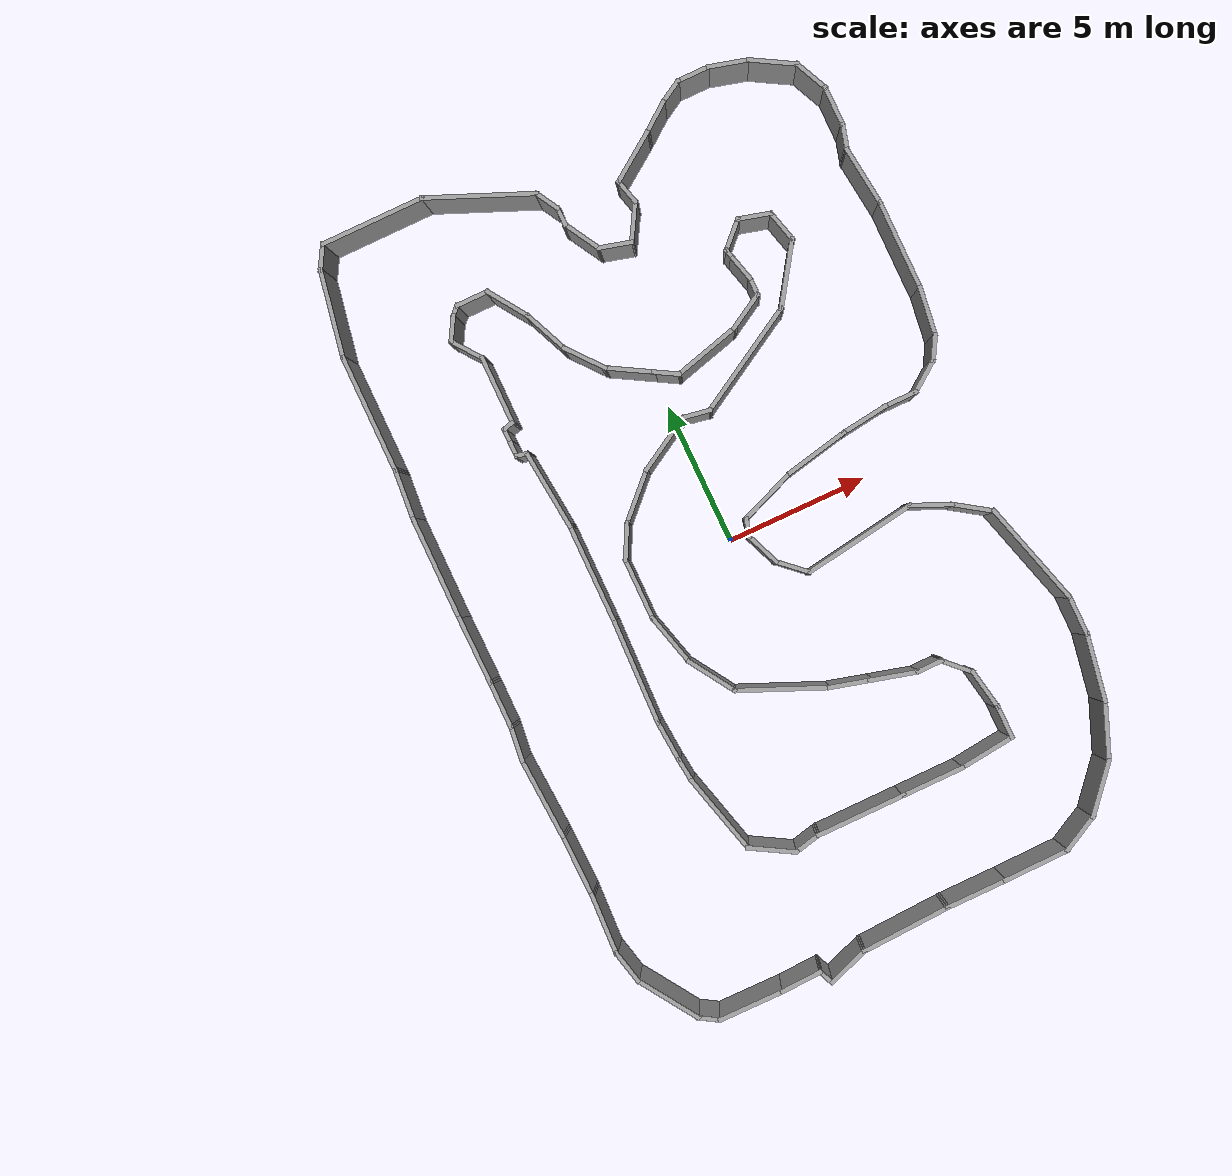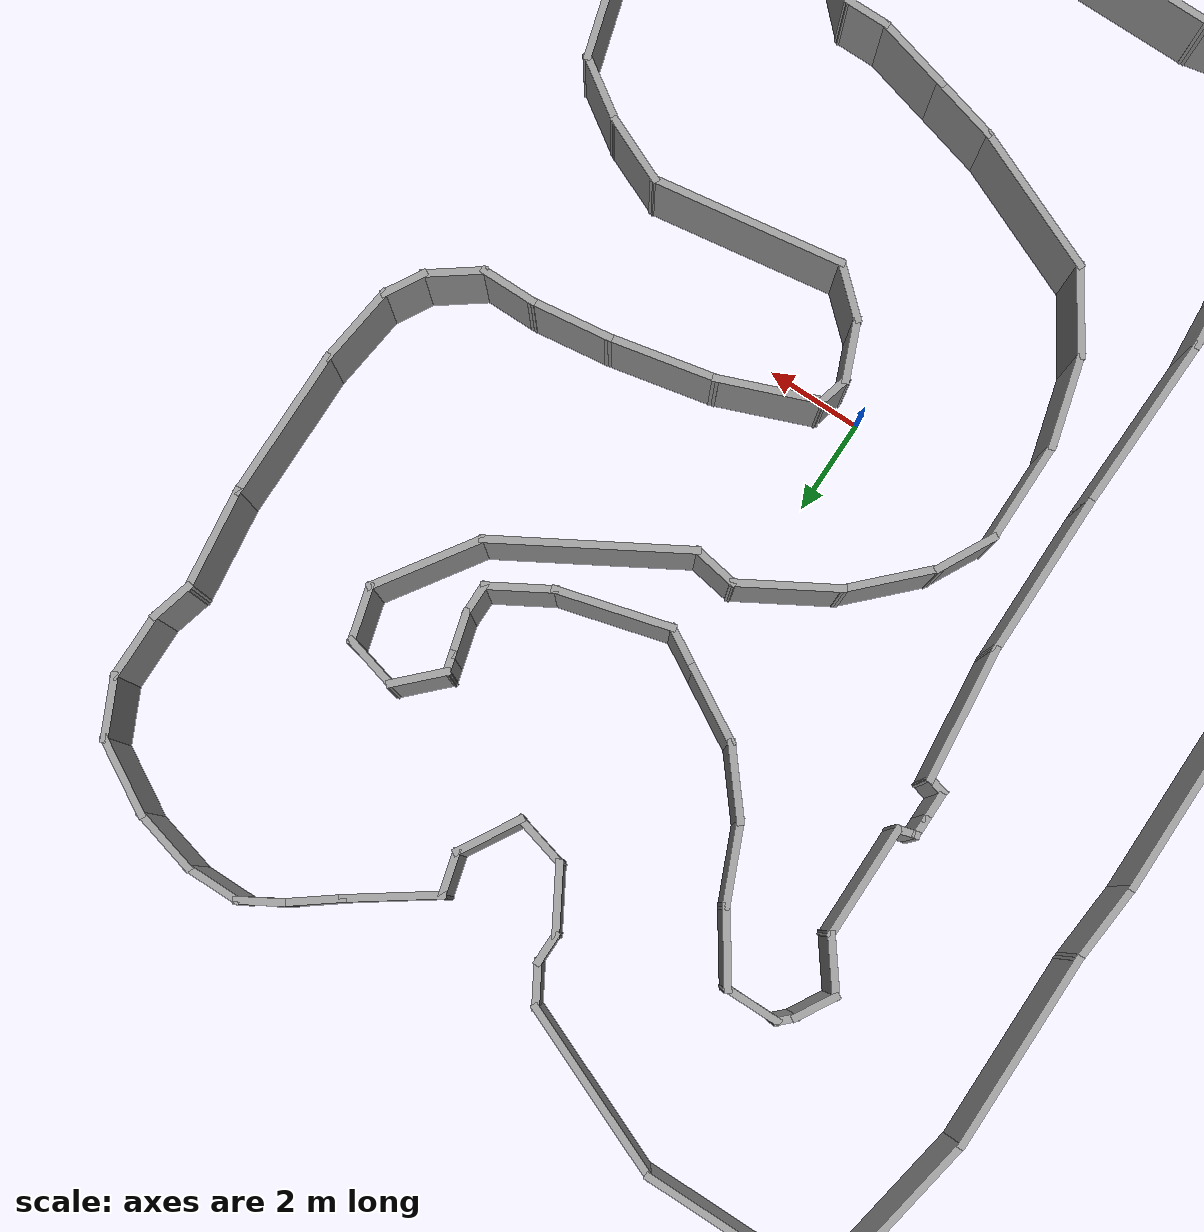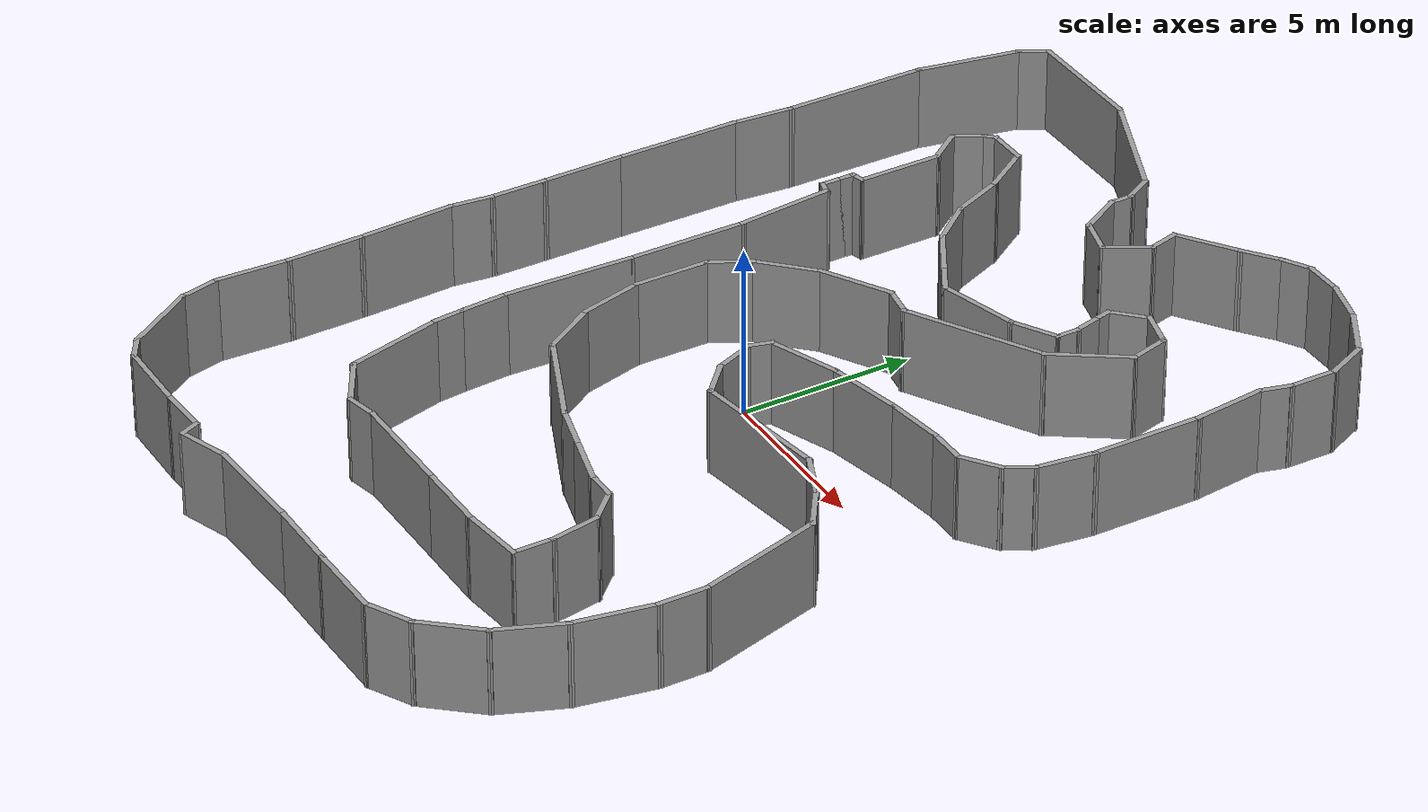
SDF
<?xml version="1.0" ?>

<sdf version="1.4">

    <model name='BuildingDefaultName'>
            <pose>0 0 0 0 -0 0</pose>
    <link name='Wall_0'>
      <collision name='Wall_0_Collision'>
        <geometry>
          <box>
            <size>1.75 0.15 2.5</size>
          </box>
        </geometry>
        <pose>0 0 1.25 0 -0 0</pose>
      </collision>
      <visual name='Wall_0_Visual'>
        <pose>0 0 1.25 0 -0 0</pose>
        <geometry>
          <box>
            <size>1.75 0.15 2.5</size>
          </box>
        </geometry>
        <material>
          <script>
            <uri>file://media/materials/scripts/gazebo.material</uri>
            <name>Gazebo/Grey</name>
          </script>
        </material>
      </visual>
      <velocity_decay>
        <linear>0</linear>
        <angular>0</angular>
      </velocity_decay>
      <pose>-9.13259 -1.69954 0 0 0 -1.5708</pose>
    </link>
    <link name='Wall_1'>
      <collision name='Wall_1_Collision'>
        <geometry>
          <box>
            <size>1.32231 0.15 2.5</size>
          </box>
        </geometry>
        <pose>0 0 1.25 0 -0 0</pose>
      </collision>
      <visual name='Wall_1_Visual'>
        <pose>0 0 1.25 0 -0 0</pose>
        <geometry>
          <box>
            <size>1.32231 0.15 2.5</size>
          </box>
        </geometry>
        <material>
          <script>
            <uri>file://media/materials/scripts/gazebo.material</uri>
            <name>Gazebo/Grey</name>
          </script>
        </material>
      </visual>
      <velocity_decay>
        <linear>0</linear>
        <angular>0</angular>
      </velocity_decay>
      <pose>-9.19833 -3.082 0 0 0 -1.68319</pose>
    </link>
    <link name='Wall_2'>
      <collision name='Wall_2_Collision'>
        <geometry>
          <box>
            <size>0.673963 0.15 2.5</size>
          </box>
        </geometry>
        <pose>0 0 1.25 0 -0 0</pose>
      </collision>
      <visual name='Wall_2_Visual'>
        <pose>0 0 1.25 0 -0 0</pose>
        <geometry>
          <box>
            <size>0.673963 0.15 2.5</size>
          </box>
        </geometry>
        <material>
          <script>
            <uri>file://media/materials/scripts/gazebo.material</uri>
            <name>Gazebo/Grey</name>
          </script>
        </material>
      </visual>
      <velocity_decay>
        <linear>0</linear>
        <angular>0</angular>
      </velocity_decay>
      <pose>-3.24793 -14.2675 0 0 0 -1.15257</pose>
    </link>
    <link name='Wall_3'>
      <collision name='Wall_3_Collision'>
        <geometry>
          <box>
            <size>2.06108 0.15 2.5</size>
          </box>
        </geometry>
        <pose>0 0 1.25 0 -0 0</pose>
      </collision>
      <visual name='Wall_3_Visual'>
        <pose>0 0 1.25 0 -0 0</pose>
        <geometry>
          <box>
            <size>2.06108 0.15 2.5</size>
          </box>
        </geometry>
        <material>
          <script>
            <uri>file://media/materials/scripts/gazebo.material</uri>
            <name>Gazebo/Grey</name>
          </script>
        </material>
      </visual>
      <velocity_decay>
        <linear>0</linear>
        <angular>0</angular>
      </velocity_decay>
      <pose>4.6394 -9.86659 0 0 0 -3.0322</pose>
    </link>
    <link name='Wall_4'>
      <collision name='Wall_4_Collision'>
        <geometry>
          <box>
            <size>2.25 0.15 2.5</size>
          </box>
        </geometry>
        <pose>0 0 1.25 0 -0 0</pose>
      </collision>
      <visual name='Wall_4_Visual'>
        <pose>0 0 1.25 0 -0 0</pose>
        <geometry>
          <box>
            <size>2.25 0.15 2.5</size>
          </box>
        </geometry>
        <material>
          <script>
            <uri>file://media/materials/scripts/gazebo.material</uri>
            <name>Gazebo/Grey</name>
          </script>
        </material>
      </visual>
      <velocity_decay>
        <linear>0</linear>
        <angular>0</angular>
      </velocity_decay>
      <pose>2.63957 -9.97091 0 0 -0 3.14159</pose>
    </link>
    <link name='Wall_5'>
      <collision name='Wall_5_Collision'>
        <geometry>
          <box>
            <size>3.25 0.15 2.5</size>
          </box>
        </geometry>
        <pose>0 0 1.25 0 -0 0</pose>
      </collision>
      <visual name='Wall_5_Visual'>
        <pose>0 0 1.25 0 -0 0</pose>
        <geometry>
          <box>
            <size>3.25 0.15 2.5</size>
          </box>
        </geometry>
        <material>
          <script>
            <uri>file://media/materials/scripts/gazebo.material</uri>
            <name>Gazebo/Grey</name>
          </script>
        </material>
      </visual>
      <velocity_decay>
        <linear>0</linear>
        <angular>0</angular>
      </velocity_decay>
      <pose>0.039574 -9.97091 0 0 -0 3.14159</pose>
    </link>
    <link name='Wall_6'>
      <collision name='Wall_6_Collision'>
        <geometry>
          <box>
            <size>1.04919 0.15 2.5</size>
          </box>
        </geometry>
        <pose>0 0 1.25 0 -0 0</pose>
      </collision>
      <visual name='Wall_6_Visual'>
        <pose>0 0 1.25 0 -0 0</pose>
        <geometry>
          <box>
            <size>1.04919 0.15 2.5</size>
          </box>
        </geometry>
        <material>
          <script>
            <uri>file://media/materials/scripts/gazebo.material</uri>
            <name>Gazebo/Grey</name>
          </script>
        </material>
      </visual>
      <velocity_decay>
        <linear>0</linear>
        <angular>0</angular>
      </velocity_decay>
      <pose>-1.94987 -10.0659 0 0 0 -2.92873</pose>
    </link>
    <link name='Wall_7'>
      <collision name='Wall_7_Collision'>
        <geometry>
          <box>
            <size>1.75 0.15 2.5</size>
          </box>
        </geometry>
        <pose>0 0 1.25 0 -0 0</pose>
      </collision>
      <visual name='Wall_7_Visual'>
        <pose>0 0 1.25 0 -0 0</pose>
        <geometry>
          <box>
            <size>1.75 0.15 2.5</size>
          </box>
        </geometry>
        <material>
          <script>
            <uri>file://media/materials/scripts/gazebo.material</uri>
            <name>Gazebo/Grey</name>
          </script>
        </material>
      </visual>
      <velocity_decay>
        <linear>0</linear>
        <angular>0</angular>
      </velocity_decay>
      <pose>-3.08214 -9.76088 0 0 -0 2.61799</pose>
    </link>
    <link name='Wall_8'>
      <collision name='Wall_8_Collision'>
        <geometry>
          <box>
            <size>3 0.15 2.5</size>
          </box>
        </geometry>
        <pose>0 0 1.25 0 -0 0</pose>
      </collision>
      <visual name='Wall_8_Visual'>
        <pose>0 0 1.25 0 -0 0</pose>
        <geometry>
          <box>
            <size>3 0.15 2.5</size>
          </box>
        </geometry>
        <material>
          <script>
            <uri>file://media/materials/scripts/gazebo.material</uri>
            <name>Gazebo/Grey</name>
          </script>
        </material>
      </visual>
      <velocity_decay>
        <linear>0</linear>
        <angular>0</angular>
      </velocity_decay>
      <pose>-4.14377 -7.98443 0 0 -0 1.8326</pose>
    </link>
    <link name='Wall_9'>
      <collision name='Wall_9_Collision'>
        <geometry>
          <box>
            <size>0.971593 0.15 2.5</size>
          </box>
        </geometry>
        <pose>0 0 1.25 0 -0 0</pose>
      </collision>
      <visual name='Wall_9_Visual'>
        <pose>0 0 1.25 0 -0 0</pose>
        <geometry>
          <box>
            <size>0.971593 0.15 2.5</size>
          </box>
        </geometry>
        <material>
          <script>
            <uri>file://media/materials/scripts/gazebo.material</uri>
            <name>Gazebo/Grey</name>
          </script>
        </material>
      </visual>
      <velocity_decay>
        <linear>0</linear>
        <angular>0</angular>
      </velocity_decay>
      <pose>-4.55908 -6.19983 0 0 -0 1.68422</pose>
    </link>
    <link name='Wall_10'>
      <collision name='Wall_10_Collision'>
        <geometry>
          <box>
            <size>1.52602 0.15 2.5</size>
          </box>
        </geometry>
        <pose>0 0 1.25 0 -0 0</pose>
      </collision>
      <visual name='Wall_10_Visual'>
        <pose>0 0 1.25 0 -0 0</pose>
        <geometry>
          <box>
            <size>1.52602 0.15 2.5</size>
          </box>
        </geometry>
        <material>
          <script>
            <uri>file://media/materials/scripts/gazebo.material</uri>
            <name>Gazebo/Grey</name>
          </script>
        </material>
      </visual>
      <velocity_decay>
        <linear>0</linear>
        <angular>0</angular>
      </velocity_decay>
      <pose>-4.65835 -5.10569 0 0 -0 1.64757</pose>
    </link>
    <link name='Wall_11'>
      <collision name='Wall_11_Collision'>
        <geometry>
          <box>
            <size>3.80308 0.15 2.5</size>
          </box>
        </geometry>
        <pose>0 0 1.25 0 -0 0</pose>
      </collision>
      <visual name='Wall_11_Visual'>
        <pose>0 0 1.25 0 -0 0</pose>
        <geometry>
          <box>
            <size>3.80308 0.15 2.5</size>
          </box>
        </geometry>
        <material>
          <script>
            <uri>file://media/materials/scripts/gazebo.material</uri>
            <name>Gazebo/Grey</name>
          </script>
        </material>
      </visual>
      <velocity_decay>
        <linear>0</linear>
        <angular>0</angular>
      </velocity_decay>
      <pose>-4.65835 -2.59393 0 0 -0 1.5419</pose>
    </link>
    <link name='Wall_12'>
      <collision name='Wall_12_Collision'>
        <geometry>
          <box>
            <size>1.61374 0.15 2.5</size>
          </box>
        </geometry>
        <pose>0 0 1.25 0 -0 0</pose>
      </collision>
      <visual name='Wall_12_Visual'>
        <pose>0 0 1.25 0 -0 0</pose>
        <geometry>
          <box>
            <size>1.61374 0.15 2.5</size>
          </box>
        </geometry>
        <material>
          <script>
            <uri>file://media/materials/scripts/gazebo.material</uri>
            <name>Gazebo/Grey</name>
          </script>
        </material>
      </visual>
      <velocity_decay>
        <linear>0</linear>
        <angular>0</angular>
      </velocity_decay>
      <pose>-2.44992 -14.2675 0 0 -0 0.333244</pose>
    </link>
    <link name='Wall_13'>
      <collision name='Wall_13_Collision'>
        <geometry>
          <box>
            <size>3.21191 0.15 2.5</size>
          </box>
        </geometry>
        <pose>0 0 1.25 0 -0 0</pose>
      </collision>
      <visual name='Wall_13_Visual'>
        <pose>0 0 1.25 0 -0 0</pose>
        <geometry>
          <box>
            <size>3.21191 0.15 2.5</size>
          </box>
        </geometry>
        <material>
          <script>
            <uri>file://media/materials/scripts/gazebo.material</uri>
            <name>Gazebo/Grey</name>
          </script>
        </material>
      </visual>
      <velocity_decay>
        <linear>0</linear>
        <angular>0</angular>
      </velocity_decay>
      <pose>-0.228806 -13.9616 0 0 -0 0.043451</pose>
    </link>
    <link name='Wall_14'>
      <collision name='Wall_14_Collision'>
        <geometry>
          <box>
            <size>2.25158 0.15 2.5</size>
          </box>
        </geometry>
        <pose>0 0 1.25 0 -0 0</pose>
      </collision>
      <visual name='Wall_14_Visual'>
        <pose>0 0 1.25 0 -0 0</pose>
        <geometry>
          <box>
            <size>2.25158 0.15 2.5</size>
          </box>
        </geometry>
        <material>
          <script>
            <uri>file://media/materials/scripts/gazebo.material</uri>
            <name>Gazebo/Grey</name>
          </script>
        </material>
      </visual>
      <velocity_decay>
        <linear>0</linear>
        <angular>0</angular>
      </velocity_decay>
      <pose>2.35141 -13.8951 0 0 -0 0</pose>
    </link>
    <link name='Wall_15'>
      <collision name='Wall_15_Collision'>
        <geometry>
          <box>
            <size>2.41117 0.15 2.5</size>
          </box>
        </geometry>
        <pose>0 0 1.25 0 -0 0</pose>
      </collision>
      <visual name='Wall_15_Visual'>
        <pose>0 0 1.25 0 -0 0</pose>
        <geometry>
          <box>
            <size>2.41117 0.15 2.5</size>
          </box>
        </geometry>
        <material>
          <script>
            <uri>file://media/materials/scripts/gazebo.material</uri>
            <name>Gazebo/Grey</name>
          </script>
        </material>
      </visual>
      <velocity_decay>
        <linear>0</linear>
        <angular>0</angular>
      </velocity_decay>
      <pose>4.53263 -13.8818 0 0 -0 0.011764</pose>
    </link>
    <link name='Wall_16'>
      <collision name='Wall_16_Collision'>
        <geometry>
          <box>
            <size>1.53014 0.15 2.5</size>
          </box>
        </geometry>
        <pose>0 0 1.25 0 -0 0</pose>
      </collision>
      <visual name='Wall_16_Visual'>
        <pose>0 0 1.25 0 -0 0</pose>
        <geometry>
          <box>
            <size>1.53014 0.15 2.5</size>
          </box>
        </geometry>
        <material>
          <script>
            <uri>file://media/materials/scripts/gazebo.material</uri>
            <name>Gazebo/Grey</name>
          </script>
        </material>
      </visual>
      <velocity_decay>
        <linear>0</linear>
        <angular>0</angular>
      </velocity_decay>
      <pose>6.27494 -13.5493 0 0 -0 0.480887</pose>
    </link>
    <link name='Wall_17'>
      <collision name='Wall_17_Collision'>
        <geometry>
          <box>
            <size>2.05428 0.15 2.5</size>
          </box>
        </geometry>
        <pose>0 0 1.25 0 -0 0</pose>
      </collision>
      <visual name='Wall_17_Visual'>
        <pose>0 0 1.25 0 -0 0</pose>
        <geometry>
          <box>
            <size>2.05428 0.15 2.5</size>
          </box>
        </geometry>
        <material>
          <script>
            <uri>file://media/materials/scripts/gazebo.material</uri>
            <name>Gazebo/Grey</name>
          </script>
        </material>
      </visual>
      <velocity_decay>
        <linear>0</linear>
        <angular>0</angular>
      </velocity_decay>
      <pose>7.51185 -12.5119 0 0 -0 0.854594</pose>
    </link>
    <link name='Wall_18'>
      <collision name='Wall_18_Collision'>
        <geometry>
          <box>
            <size>2.09618 0.15 2.5</size>
          </box>
        </geometry>
        <pose>0 0 1.25 0 -0 0</pose>
      </collision>
      <visual name='Wall_18_Visual'>
        <pose>0 0 1.25 0 -0 0</pose>
        <geometry>
          <box>
            <size>2.09618 0.15 2.5</size>
          </box>
        </geometry>
        <material>
          <script>
            <uri>file://media/materials/scripts/gazebo.material</uri>
            <name>Gazebo/Grey</name>
          </script>
        </material>
      </visual>
      <velocity_decay>
        <linear>0</linear>
        <angular>0</angular>
      </velocity_decay>
      <pose>8.49606 -10.8893 0 0 -0 1.19283</pose>
    </link>
    <link name='Wall_19'>
      <collision name='Wall_19_Collision'>
        <geometry>
          <box>
            <size>2.41976 0.15 2.5</size>
          </box>
        </geometry>
        <pose>0 0 1.25 0 -0 0</pose>
      </collision>
      <visual name='Wall_19_Visual'>
        <pose>0 0 1.25 0 -0 0</pose>
        <geometry>
          <box>
            <size>2.41976 0.15 2.5</size>
          </box>
        </geometry>
        <material>
          <script>
            <uri>file://media/materials/scripts/gazebo.material</uri>
            <name>Gazebo/Grey</name>
          </script>
        </material>
      </visual>
      <velocity_decay>
        <linear>0</linear>
        <angular>0</angular>
      </velocity_decay>
      <pose>9.05466 -8.86771 0 0 -0 1.39409</pose>
    </link>
    <link name='Wall_20'>
      <collision name='Wall_20_Collision'>
        <geometry>
          <box>
            <size>1.5 0.15 2.5</size>
          </box>
        </geometry>
        <pose>0 0 1.25 0 -0 0</pose>
      </collision>
      <visual name='Wall_20_Visual'>
        <pose>0 0 1.25 0 -0 0</pose>
        <geometry>
          <box>
            <size>1.5 0.15 2.5</size>
          </box>
        </geometry>
        <material>
          <script>
            <uri>file://media/materials/scripts/gazebo.material</uri>
            <name>Gazebo/Grey</name>
          </script>
        </material>
      </visual>
      <velocity_decay>
        <linear>0</linear>
        <angular>0</angular>
      </velocity_decay>
      <pose>9.25417 -7.0755 0 0 -0 1.5708</pose>
    </link>
    <link name='Wall_21'>
      <collision name='Wall_21_Collision'>
        <geometry>
          <box>
            <size>2.93747 0.15 2.5</size>
          </box>
        </geometry>
        <pose>0 0 1.25 0 -0 0</pose>
      </collision>
      <visual name='Wall_21_Visual'>
        <pose>0 0 1.25 0 -0 0</pose>
        <geometry>
          <box>
            <size>2.93747 0.15 2.5</size>
          </box>
        </geometry>
        <material>
          <script>
            <uri>file://media/materials/scripts/gazebo.material</uri>
            <name>Gazebo/Grey</name>
          </script>
        </material>
      </visual>
      <velocity_decay>
        <linear>0</linear>
        <angular>0</angular>
      </velocity_decay>
      <pose>-9.18202 -5.05577 0 0 0 -1.51189</pose>
    </link>
    <link name='Wall_22'>
      <collision name='Wall_22_Collision'>
        <geometry>
          <box>
            <size>3.89422 0.15 2.5</size>
          </box>
        </geometry>
        <pose>0 0 1.25 0 -0 0</pose>
      </collision>
      <visual name='Wall_22_Visual'>
        <pose>0 0 1.25 0 -0 0</pose>
        <geometry>
          <box>
            <size>3.89422 0.15 2.5</size>
          </box>
        </geometry>
        <material>
          <script>
            <uri>file://media/materials/scripts/gazebo.material</uri>
            <name>Gazebo/Grey</name>
          </script>
        </material>
      </visual>
      <velocity_decay>
        <linear>0</linear>
        <angular>0</angular>
      </velocity_decay>
      <pose>8.73546 -4.60168 0 0 -0 1.85154</pose>
    </link>
    <link name='Wall_23'>
      <collision name='Wall_23_Collision'>
        <geometry>
          <box>
            <size>1.52963 0.15 2.5</size>
          </box>
        </geometry>
        <pose>0 0 1.25 0 -0 0</pose>
      </collision>
      <visual name='Wall_23_Visual'>
        <pose>0 0 1.25 0 -0 0</pose>
        <geometry>
          <box>
            <size>1.52963 0.15 2.5</size>
          </box>
        </geometry>
        <material>
          <script>
            <uri>file://media/materials/scripts/gazebo.material</uri>
            <name>Gazebo/Grey</name>
          </script>
        </material>
      </visual>
      <velocity_decay>
        <linear>0</linear>
        <angular>0</angular>
      </velocity_decay>
      <pose>7.64485 -2.41716 0 0 -0 2.54824</pose>
    </link>
    <link name='Wall_24'>
      <collision name='Wall_24_Collision'>
        <geometry>
          <box>
            <size>1.54366 0.15 2.5</size>
          </box>
        </geometry>
        <pose>0 0 1.25 0 -0 0</pose>
      </collision>
      <visual name='Wall_24_Visual'>
        <pose>0 0 1.25 0 -0 0</pose>
        <geometry>
          <box>
            <size>1.54366 0.15 2.5</size>
          </box>
        </geometry>
        <material>
          <script>
            <uri>file://media/materials/scripts/gazebo.material</uri>
            <name>Gazebo/Grey</name>
          </script>
        </material>
      </visual>
      <velocity_decay>
        <linear>0</linear>
        <angular>0</angular>
      </velocity_decay>
      <pose>6.43454 -1.75215 0 0 -0 2.72918</pose>
    </link>
    <link name='Wall_25'>
      <collision name='Wall_25_Collision'>
        <geometry>
          <box>
            <size>4.10378 0.15 2.5</size>
          </box>
        </geometry>
        <pose>0 0 1.25 0 -0 0</pose>
      </collision>
      <visual name='Wall_25_Visual'>
        <pose>0 0 1.25 0 -0 0</pose>
        <geometry>
          <box>
            <size>4.10378 0.15 2.5</size>
          </box>
        </geometry>
        <material>
          <script>
            <uri>file://media/materials/scripts/gazebo.material</uri>
            <name>Gazebo/Grey</name>
          </script>
        </material>
      </visual>
      <velocity_decay>
        <linear>0</linear>
        <angular>0</angular>
      </velocity_decay>
      <pose>3.84102 -1.76545 0 0 0 -2.99303</pose>
    </link>
    <link name='Wall_26'>
      <collision name='Wall_26_Collision'>
        <geometry>
          <box>
            <size>1.29875 0.15 2.5</size>
          </box>
        </geometry>
        <pose>0 0 1.25 0 -0 0</pose>
      </collision>
      <visual name='Wall_26_Visual'>
        <pose>0 0 1.25 0 -0 0</pose>
        <geometry>
          <box>
            <size>1.29875 0.15 2.5</size>
          </box>
        </geometry>
        <material>
          <script>
            <uri>file://media/materials/scripts/gazebo.material</uri>
            <name>Gazebo/Grey</name>
          </script>
        </material>
      </visual>
      <velocity_decay>
        <linear>0</linear>
        <angular>0</angular>
      </velocity_decay>
      <pose>1.46031 -1.67235 0 0 -0 2.40534</pose>
    </link>
    <link name='Wall_27'>
      <collision name='Wall_27_Collision'>
        <geometry>
          <box>
            <size>1.35526 0.15 2.5</size>
          </box>
        </geometry>
        <pose>0 0 1.25 0 -0 0</pose>
      </collision>
      <visual name='Wall_27_Visual'>
        <pose>0 0 1.25 0 -0 0</pose>
        <geometry>
          <box>
            <size>1.35526 0.15 2.5</size>
          </box>
        </geometry>
        <material>
          <script>
            <uri>file://media/materials/scripts/gazebo.material</uri>
            <name>Gazebo/Grey</name>
          </script>
        </material>
      </visual>
      <velocity_decay>
        <linear>0</linear>
        <angular>0</angular>
      </velocity_decay>
      <pose>0.808602 -0.728047 0 0 -0 1.9554</pose>
    </link>
    <link name='Wall_28'>
      <collision name='Wall_28_Collision'>
        <geometry>
          <box>
            <size>0.75 0.15 2.5</size>
          </box>
        </geometry>
        <pose>0 0 1.25 0 -0 0</pose>
      </collision>
      <visual name='Wall_28_Visual'>
        <pose>0 0 1.25 0 -0 0</pose>
        <geometry>
          <box>
            <size>0.75 0.15 2.5</size>
          </box>
        </geometry>
        <material>
          <script>
            <uri>file://media/materials/scripts/gazebo.material</uri>
            <name>Gazebo/Grey</name>
          </script>
        </material>
      </visual>
      <velocity_decay>
        <linear>0</linear>
        <angular>0</angular>
      </velocity_decay>
      <pose>0.660146 0.120334 0 0 -0 1.309</pose>
    </link>
    <link name='Wall_29'>
      <collision name='Wall_29_Collision'>
        <geometry>
          <box>
            <size>2.23581 0.15 2.5</size>
          </box>
        </geometry>
        <pose>0 0 1.25 0 -0 0</pose>
      </collision>
      <visual name='Wall_29_Visual'>
        <pose>0 0 1.25 0 -0 0</pose>
        <geometry>
          <box>
            <size>2.23581 0.15 2.5</size>
          </box>
        </geometry>
        <material>
          <script>
            <uri>file://media/materials/scripts/gazebo.material</uri>
            <name>Gazebo/Grey</name>
          </script>
        </material>
      </visual>
      <velocity_decay>
        <linear>0</linear>
        <angular>0</angular>
      </velocity_decay>
      <pose>1.71085 0.785339 0 0 -0 0.368044</pose>
    </link>
    <link name='Wall_30'>
      <collision name='Wall_30_Collision'>
        <geometry>
          <box>
            <size>2.35156 0.15 2.5</size>
          </box>
        </geometry>
        <pose>0 0 1.25 0 -0 0</pose>
      </collision>
      <visual name='Wall_30_Visual'>
        <pose>0 0 1.25 0 -0 0</pose>
        <geometry>
          <box>
            <size>2.35156 0.15 2.5</size>
          </box>
        </geometry>
        <material>
          <script>
            <uri>file://media/materials/scripts/gazebo.material</uri>
            <name>Gazebo/Grey</name>
          </script>
        </material>
      </visual>
      <velocity_decay>
        <linear>0</linear>
        <angular>0</angular>
      </velocity_decay>
      <pose>3.76122 1.38667 0 0 -0 0.206874</pose>
    </link>
    <link name='Wall_31'>
      <collision name='Wall_31_Collision'>
        <geometry>
          <box>
            <size>1.78651 0.15 2.5</size>
          </box>
        </geometry>
        <pose>0 0 1.25 0 -0 0</pose>
      </collision>
      <visual name='Wall_31_Visual'>
        <pose>0 0 1.25 0 -0 0</pose>
        <geometry>
          <box>
            <size>1.78651 0.15 2.5</size>
          </box>
        </geometry>
        <material>
          <script>
            <uri>file://media/materials/scripts/gazebo.material</uri>
            <name>Gazebo/Grey</name>
          </script>
        </material>
      </visual>
      <velocity_decay>
        <linear>0</linear>
        <angular>0</angular>
      </velocity_decay>
      <pose>5.64984 1.71917 0 0 -0 0.130403</pose>
    </link>
    <link name='Wall_32'>
      <collision name='Wall_32_Collision'>
        <geometry>
          <box>
            <size>2.30527 0.15 2.5</size>
          </box>
        </geometry>
        <pose>0 0 1.25 0 -0 0</pose>
      </collision>
      <visual name='Wall_32_Visual'>
        <pose>0 0 1.25 0 -0 0</pose>
        <geometry>
          <box>
            <size>2.30527 0.15 2.5</size>
          </box>
        </geometry>
        <material>
          <script>
            <uri>file://media/materials/scripts/gazebo.material</uri>
            <name>Gazebo/Grey</name>
          </script>
        </material>
      </visual>
      <velocity_decay>
        <linear>0</linear>
        <angular>0</angular>
      </velocity_decay>
      <pose>-9.07337 -7.5244 0 0 0 -1.54611</pose>
    </link>
    <link name='Wall_33'>
      <collision name='Wall_33_Collision'>
        <geometry>
          <box>
            <size>1.25 0.15 2.5</size>
          </box>
        </geometry>
        <pose>0 0 1.25 0 -0 0</pose>
      </collision>
      <visual name='Wall_33_Visual'>
        <pose>0 0 1.25 0 -0 0</pose>
        <geometry>
          <box>
            <size>1.25 0.15 2.5</size>
          </box>
        </geometry>
        <material>
          <script>
            <uri>file://media/materials/scripts/gazebo.material</uri>
            <name>Gazebo/Grey</name>
          </script>
        </material>
      </visual>
      <velocity_decay>
        <linear>0</linear>
        <angular>0</angular>
      </velocity_decay>
      <pose>7.01114 1.82557 0 0 -0 0</pose>
    </link>
    <link name='Wall_34'>
      <collision name='Wall_34_Collision'>
        <geometry>
          <box>
            <size>1.32364 0.15 2.5</size>
          </box>
        </geometry>
        <pose>0 0 1.25 0 -0 0</pose>
      </collision>
      <visual name='Wall_34_Visual'>
        <pose>0 0 1.25 0 -0 0</pose>
        <geometry>
          <box>
            <size>1.32364 0.15 2.5</size>
          </box>
        </geometry>
        <material>
          <script>
            <uri>file://media/materials/scripts/gazebo.material</uri>
            <name>Gazebo/Grey</name>
          </script>
        </material>
      </visual>
      <velocity_decay>
        <linear>0</linear>
        <angular>0</angular>
      </velocity_decay>
      <pose>8.03525 2.17137 0 0 -0 0.63017</pose>
    </link>
    <link name='Wall_35'>
      <collision name='Wall_35_Collision'>
        <geometry>
          <box>
            <size>1 0.15 2.5</size>
          </box>
        </geometry>
        <pose>0 0 1.25 0 -0 0</pose>
      </collision>
      <visual name='Wall_35_Visual'>
        <pose>0 0 1.25 0 -0 0</pose>
        <geometry>
          <box>
            <size>1 0.15 2.5</size>
          </box>
        </geometry>
        <material>
          <script>
            <uri>file://media/materials/scripts/gazebo.material</uri>
            <name>Gazebo/Grey</name>
          </script>
        </material>
      </visual>
      <velocity_decay>
        <linear>0</linear>
        <angular>0</angular>
      </velocity_decay>
      <pose>8.72186 2.88524 0 0 -0 1.0472</pose>
    </link>
    <link name='Wall_36'>
      <collision name='Wall_36_Collision'>
        <geometry>
          <box>
            <size>1.7952 0.15 2.5</size>
          </box>
        </geometry>
        <pose>0 0 1.25 0 -0 0</pose>
      </collision>
      <visual name='Wall_36_Visual'>
        <pose>0 0 1.25 0 -0 0</pose>
        <geometry>
          <box>
            <size>1.7952 0.15 2.5</size>
          </box>
        </geometry>
        <material>
          <script>
            <uri>file://media/materials/scripts/gazebo.material</uri>
            <name>Gazebo/Grey</name>
          </script>
        </material>
      </visual>
      <velocity_decay>
        <linear>0</linear>
        <angular>0</angular>
      </velocity_decay>
      <pose>9.04106 4.06895 0 0 -0 1.44072</pose>
    </link>
    <link name='Wall_37'>
      <collision name='Wall_37_Collision'>
        <geometry>
          <box>
            <size>3.25 0.15 2.5</size>
          </box>
        </geometry>
        <pose>0 0 1.25 0 -0 0</pose>
      </collision>
      <visual name='Wall_37_Visual'>
        <pose>0 0 1.25 0 -0 0</pose>
        <geometry>
          <box>
            <size>3.25 0.15 2.5</size>
          </box>
        </geometry>
        <material>
          <script>
            <uri>file://media/materials/scripts/gazebo.material</uri>
            <name>Gazebo/Grey</name>
          </script>
        </material>
      </visual>
      <velocity_decay>
        <linear>0</linear>
        <angular>0</angular>
      </velocity_decay>
      <pose>9.14776 6.43459 0 0 -0 1.5708</pose>
    </link>
    <link name='Wall_38'>
      <collision name='Wall_38_Collision'>
        <geometry>
          <box>
            <size>2.19788 0.15 2.5</size>
          </box>
        </geometry>
        <pose>0 0 1.25 0 -0 0</pose>
      </collision>
      <visual name='Wall_38_Visual'>
        <pose>0 0 1.25 0 -0 0</pose>
        <geometry>
          <box>
            <size>2.19788 0.15 2.5</size>
          </box>
        </geometry>
        <material>
          <script>
            <uri>file://media/materials/scripts/gazebo.material</uri>
            <name>Gazebo/Grey</name>
          </script>
        </material>
      </visual>
      <velocity_decay>
        <linear>0</linear>
        <angular>0</angular>
      </velocity_decay>
      <pose>9.02806 9.00151 0 0 -0 1.68797</pose>
    </link>
    <link name='Wall_39'>
      <collision name='Wall_39_Collision'>
        <geometry>
          <box>
            <size>1 0.15 2.5</size>
          </box>
        </geometry>
        <pose>0 0 1.25 0 -0 0</pose>
      </collision>
      <visual name='Wall_39_Visual'>
        <pose>0 0 1.25 0 -0 0</pose>
        <geometry>
          <box>
            <size>1 0.15 2.5</size>
          </box>
        </geometry>
        <material>
          <script>
            <uri>file://media/materials/scripts/gazebo.material</uri>
            <name>Gazebo/Grey</name>
          </script>
        </material>
      </visual>
      <velocity_decay>
        <linear>0</linear>
        <angular>0</angular>
      </velocity_decay>
      <pose>9.01836 10.429 0 0 -0 1.309</pose>
    </link>
    <link name='Wall_40'>
      <collision name='Wall_40_Collision'>
        <geometry>
          <box>
            <size>1.5 0.15 2.5</size>
          </box>
        </geometry>
        <pose>0 0 1.25 0 -0 0</pose>
      </collision>
      <visual name='Wall_40_Visual'>
        <pose>0 0 1.25 0 -0 0</pose>
        <geometry>
          <box>
            <size>1.5 0.15 2.5</size>
          </box>
        </geometry>
        <material>
          <script>
            <uri>file://media/materials/scripts/gazebo.material</uri>
            <name>Gazebo/Grey</name>
          </script>
        </material>
      </visual>
      <velocity_decay>
        <linear>0</linear>
        <angular>0</angular>
      </velocity_decay>
      <pose>9.12836 11.5145 0 0 -0 1.5708</pose>
    </link>
    <link name='Wall_41'>
      <collision name='Wall_41_Collision'>
        <geometry>
          <box>
            <size>1.36429 0.15 2.5</size>
          </box>
        </geometry>
        <pose>0 0 1.25 0 -0 0</pose>
      </collision>
      <visual name='Wall_41_Visual'>
        <pose>0 0 1.25 0 -0 0</pose>
        <geometry>
          <box>
            <size>1.36429 0.15 2.5</size>
          </box>
        </geometry>
        <material>
          <script>
            <uri>file://media/materials/scripts/gazebo.material</uri>
            <name>Gazebo/Grey</name>
          </script>
        </material>
      </visual>
      <velocity_decay>
        <linear>0</linear>
        <angular>0</angular>
      </velocity_decay>
      <pose>8.87206 12.7399 0 0 -0 2.0066</pose>
    </link>
    <link name='Wall_42'>
      <collision name='Wall_42_Collision'>
        <geometry>
          <box>
            <size>1.75 0.15 2.5</size>
          </box>
        </geometry>
        <pose>0 0 1.25 0 -0 0</pose>
      </collision>
      <visual name='Wall_42_Visual'>
        <pose>0 0 1.25 0 -0 0</pose>
        <geometry>
          <box>
            <size>1.75 0.15 2.5</size>
          </box>
        </geometry>
        <material>
          <script>
            <uri>file://media/materials/scripts/gazebo.material</uri>
            <name>Gazebo/Grey</name>
          </script>
        </material>
      </visual>
      <velocity_decay>
        <linear>0</linear>
        <angular>0</angular>
      </velocity_decay>
      <pose>7.92294 13.6903 0 0 -0 2.61799</pose>
    </link>
    <link name='Wall_43'>
      <collision name='Wall_43_Collision'>
        <geometry>
          <box>
            <size>2.19977 0.15 2.5</size>
          </box>
        </geometry>
        <pose>0 0 1.25 0 -0 0</pose>
      </collision>
      <visual name='Wall_43_Visual'>
        <pose>0 0 1.25 0 -0 0</pose>
        <geometry>
          <box>
            <size>2.19977 0.15 2.5</size>
          </box>
        </geometry>
        <material>
          <script>
            <uri>file://media/materials/scripts/gazebo.material</uri>
            <name>Gazebo/Grey</name>
          </script>
        </material>
      </visual>
      <velocity_decay>
        <linear>0</linear>
        <angular>0</angular>
      </velocity_decay>
      <pose>-9.08667 -9.62581 0 0 0 -1.60974</pose>
    </link>
    <link name='Wall_44'>
      <collision name='Wall_44_Collision'>
        <geometry>
          <box>
            <size>1.5 0.15 2.5</size>
          </box>
        </geometry>
        <pose>0 0 1.25 0 -0 0</pose>
      </collision>
      <visual name='Wall_44_Visual'>
        <pose>0 0 1.25 0 -0 0</pose>
        <geometry>
          <box>
            <size>1.5 0.15 2.5</size>
          </box>
        </geometry>
        <material>
          <script>
            <uri>file://media/materials/scripts/gazebo.material</uri>
            <name>Gazebo/Grey</name>
          </script>
        </material>
      </visual>
      <velocity_decay>
        <linear>0</linear>
        <angular>0</angular>
      </velocity_decay>
      <pose>6.57812 14.265 0 0 -0 2.87979</pose>
    </link>
    <link name='Wall_45'>
      <collision name='Wall_45_Collision'>
        <geometry>
          <box>
            <size>1.25 0.15 2.5</size>
          </box>
        </geometry>
        <pose>0 0 1.25 0 -0 0</pose>
      </collision>
      <visual name='Wall_45_Visual'>
        <pose>0 0 1.25 0 -0 0</pose>
        <geometry>
          <box>
            <size>1.25 0.15 2.5</size>
          </box>
        </geometry>
        <material>
          <script>
            <uri>file://media/materials/scripts/gazebo.material</uri>
            <name>Gazebo/Grey</name>
          </script>
        </material>
      </visual>
      <velocity_decay>
        <linear>0</linear>
        <angular>0</angular>
      </velocity_decay>
      <pose>5.37612 14.4397 0 0 -0 3.14159</pose>
    </link>
    <link name='Wall_46'>
      <collision name='Wall_46_Collision'>
        <geometry>
          <box>
            <size>1 0.15 2.5</size>
          </box>
        </geometry>
        <pose>0 0 1.25 0 -0 0</pose>
      </collision>
      <visual name='Wall_46_Visual'>
        <pose>0 0 1.25 0 -0 0</pose>
        <geometry>
          <box>
            <size>1 0.15 2.5</size>
          </box>
        </geometry>
        <material>
          <script>
            <uri>file://media/materials/scripts/gazebo.material</uri>
            <name>Gazebo/Grey</name>
          </script>
        </material>
      </visual>
      <velocity_decay>
        <linear>0</linear>
        <angular>0</angular>
      </velocity_decay>
      <pose>4.45806 14.2272 0 0 0 -2.61799</pose>
    </link>
    <link name='Wall_47'>
      <collision name='Wall_47_Collision'>
        <geometry>
          <box>
            <size>1.28671 0.15 2.5</size>
          </box>
        </geometry>
        <pose>0 0 1.25 0 -0 0</pose>
      </collision>
      <visual name='Wall_47_Visual'>
        <pose>0 0 1.25 0 -0 0</pose>
        <geometry>
          <box>
            <size>1.28671 0.15 2.5</size>
          </box>
        </geometry>
        <material>
          <script>
            <uri>file://media/materials/scripts/gazebo.material</uri>
            <name>Gazebo/Grey</name>
          </script>
        </material>
      </visual>
      <velocity_decay>
        <linear>0</linear>
        <angular>0</angular>
      </velocity_decay>
      <pose>3.63675 13.6717 0 0 0 -2.4939</pose>
    </link>
    <link name='Wall_48'>
      <collision name='Wall_48_Collision'>
        <geometry>
          <box>
            <size>2.03405 0.15 2.5</size>
          </box>
        </geometry>
        <pose>0 0 1.25 0 -0 0</pose>
      </collision>
      <visual name='Wall_48_Visual'>
        <pose>0 0 1.25 0 -0 0</pose>
        <geometry>
          <box>
            <size>2.03405 0.15 2.5</size>
          </box>
        </geometry>
        <material>
          <script>
            <uri>file://media/materials/scripts/gazebo.material</uri>
            <name>Gazebo/Grey</name>
          </script>
        </material>
      </visual>
      <velocity_decay>
        <linear>0</linear>
        <angular>0</angular>
      </velocity_decay>
      <pose>2.41262 12.7874 0 0 0 -2.52927</pose>
    </link>
    <link name='Wall_49'>
      <collision name='Wall_49_Collision'>
        <geometry>
          <box>
            <size>1 0.15 2.5</size>
          </box>
        </geometry>
        <pose>0 0 1.25 0 -0 0</pose>
      </collision>
      <visual name='Wall_49_Visual'>
        <pose>0 0 1.25 0 -0 0</pose>
        <geometry>
          <box>
            <size>1 0.15 2.5</size>
          </box>
        </geometry>
        <material>
          <script>
            <uri>file://media/materials/scripts/gazebo.material</uri>
            <name>Gazebo/Grey</name>
          </script>
        </material>
      </visual>
      <velocity_decay>
        <linear>0</linear>
        <angular>0</angular>
      </velocity_decay>
      <pose>1.75175 11.8354 0 0 0 -1.309</pose>
    </link>
    <link name='Wall_50'>
      <collision name='Wall_50_Collision'>
        <geometry>
          <box>
            <size>1.5 0.15 2.5</size>
          </box>
        </geometry>
        <pose>0 0 1.25 0 -0 0</pose>
      </collision>
      <visual name='Wall_50_Visual'>
        <pose>0 0 1.25 0 -0 0</pose>
        <geometry>
          <box>
            <size>1.5 0.15 2.5</size>
          </box>
        </geometry>
        <material>
          <script>
            <uri>file://media/materials/scripts/gazebo.material</uri>
            <name>Gazebo/Grey</name>
          </script>
        </material>
      </visual>
      <velocity_decay>
        <linear>0</linear>
        <angular>0</angular>
      </velocity_decay>
      <pose>1.52425 10.8403 0 0 0 -2.0944</pose>
    </link>
    <link name='Wall_51'>
      <collision name='Wall_51_Collision'>
        <geometry>
          <box>
            <size>1.25 0.15 2.5</size>
          </box>
        </geometry>
        <pose>0 0 1.25 0 -0 0</pose>
      </collision>
      <visual name='Wall_51_Visual'>
        <pose>0 0 1.25 0 -0 0</pose>
        <geometry>
          <box>
            <size>1.25 0.15 2.5</size>
          </box>
        </geometry>
        <material>
          <script>
            <uri>file://media/materials/scripts/gazebo.material</uri>
            <name>Gazebo/Grey</name>
          </script>
        </material>
      </visual>
      <velocity_decay>
        <linear>0</linear>
        <angular>0</angular>
      </velocity_decay>
      <pose>0.655486 10.3981 0 0 -0 2.87979</pose>
    </link>
    <link name='Wall_52'>
      <collision name='Wall_52_Collision'>
        <geometry>
          <box>
            <size>1.5 0.15 2.5</size>
          </box>
        </geometry>
        <pose>0 0 1.25 0 -0 0</pose>
      </collision>
      <visual name='Wall_52_Visual'>
        <pose>0 0 1.25 0 -0 0</pose>
        <geometry>
          <box>
            <size>1.5 0.15 2.5</size>
          </box>
        </geometry>
        <material>
          <script>
            <uri>file://media/materials/scripts/gazebo.material</uri>
            <name>Gazebo/Grey</name>
          </script>
        </material>
      </visual>
      <velocity_decay>
        <linear>0</linear>
        <angular>0</angular>
      </velocity_decay>
      <pose>-0.213273 11.125 0 0 -0 2.0944</pose>
    </link>
    <link name='Wall_53'>
      <collision name='Wall_53_Collision'>
        <geometry>
          <box>
            <size>0.75 0.15 2.5</size>
          </box>
        </geometry>
        <pose>0 0 1.25 0 -0 0</pose>
      </collision>
      <visual name='Wall_53_Visual'>
        <pose>0 0 1.25 0 -0 0</pose>
        <geometry>
          <box>
            <size>0.75 0.15 2.5</size>
          </box>
        </geometry>
        <material>
          <script>
            <uri>file://media/materials/scripts/gazebo.material</uri>
            <name>Gazebo/Grey</name>
          </script>
        </material>
      </visual>
      <velocity_decay>
        <linear>0</linear>
        <angular>0</angular>
      </velocity_decay>
      <pose>-0.550773 12.0096 0 0 -0 1.5708</pose>
    </link>
    <link name='Wall_54'>
      <collision name='Wall_54_Collision'>
        <geometry>
          <box>
            <size>1.29844 0.15 2.5</size>
          </box>
        </geometry>
        <pose>0 0 1.25 0 -0 0</pose>
      </collision>
      <visual name='Wall_54_Visual'>
        <pose>0 0 1.25 0 -0 0</pose>
        <geometry>
          <box>
            <size>1.29844 0.15 2.5</size>
          </box>
        </geometry>
        <material>
          <script>
            <uri>file://media/materials/scripts/gazebo.material</uri>
            <name>Gazebo/Grey</name>
          </script>
        </material>
      </visual>
      <velocity_decay>
        <linear>0</linear>
        <angular>0</angular>
      </velocity_decay>
      <pose>-8.99357 -11.2085 0 0 0 -1.33705</pose>
    </link>
    <link name='Wall_55'>
      <collision name='Wall_55_Collision'>
        <geometry>
          <box>
            <size>1 0.15 2.5</size>
          </box>
        </geometry>
        <pose>0 0 1.25 0 -0 0</pose>
      </collision>
      <visual name='Wall_55_Visual'>
        <pose>0 0 1.25 0 -0 0</pose>
        <geometry>
          <box>
            <size>1 0.15 2.5</size>
          </box>
        </geometry>
        <material>
          <script>
            <uri>file://media/materials/scripts/gazebo.material</uri>
            <name>Gazebo/Grey</name>
          </script>
        </material>
      </visual>
      <velocity_decay>
        <linear>0</linear>
        <angular>0</angular>
      </velocity_decay>
      <pose>-0.763273 12.6777 0 0 -0 2.0944</pose>
    </link>
    <link name='Wall_56'>
      <collision name='Wall_56_Collision'>
        <geometry>
          <box>
            <size>3.91935 0.15 2.5</size>
          </box>
        </geometry>
        <pose>0 0 1.25 0 -0 0</pose>
      </collision>
      <visual name='Wall_56_Visual'>
        <pose>0 0 1.25 0 -0 0</pose>
        <geometry>
          <box>
            <size>3.91935 0.15 2.5</size>
          </box>
        </geometry>
        <material>
          <script>
            <uri>file://media/materials/scripts/gazebo.material</uri>
            <name>Gazebo/Grey</name>
          </script>
        </material>
      </visual>
      <velocity_decay>
        <linear>0</linear>
        <angular>0</angular>
      </velocity_decay>
      <pose>-2.7138 13.7746 0 0 -0 2.7445</pose>
    </link>
    <link name='Wall_57'>
      <collision name='Wall_57_Collision'>
        <geometry>
          <box>
            <size>3.75 0.15 2.5</size>
          </box>
        </geometry>
        <pose>0 0 1.25 0 -0 0</pose>
      </collision>
      <visual name='Wall_57_Visual'>
        <pose>0 0 1.25 0 -0 0</pose>
        <geometry>
          <box>
            <size>3.75 0.15 2.5</size>
          </box>
        </geometry>
        <material>
          <script>
            <uri>file://media/materials/scripts/gazebo.material</uri>
            <name>Gazebo/Grey</name>
          </script>
        </material>
      </visual>
      <velocity_decay>
        <linear>0</linear>
        <angular>0</angular>
      </velocity_decay>
      <pose>-6.25183 14.5035 0 0 -0 3.14159</pose>
    </link>
    <link name='Wall_58'>
      <collision name='Wall_58_Collision'>
        <geometry>
          <box>
            <size>1 0.15 2.5</size>
          </box>
        </geometry>
        <pose>0 0 1.25 0 -0 0</pose>
      </collision>
      <visual name='Wall_58_Visual'>
        <pose>0 0 1.25 0 -0 0</pose>
        <geometry>
          <box>
            <size>1 0.15 2.5</size>
          </box>
        </geometry>
        <material>
          <script>
            <uri>file://media/materials/scripts/gazebo.material</uri>
            <name>Gazebo/Grey</name>
          </script>
        </material>
      </visual>
      <velocity_decay>
        <linear>0</linear>
        <angular>0</angular>
      </velocity_decay>
      <pose>-8.26432 14.1354 0 0 0 -2.0944</pose>
    </link>
    <link name='Wall_59'>
      <collision name='Wall_59_Collision'>
        <geometry>
          <box>
            <size>3.13491 0.15 2.5</size>
          </box>
        </geometry>
        <pose>0 0 1.25 0 -0 0</pose>
      </collision>
      <visual name='Wall_59_Visual'>
        <pose>0 0 1.25 0 -0 0</pose>
        <geometry>
          <box>
            <size>3.13491 0.15 2.5</size>
          </box>
        </geometry>
        <material>
          <script>
            <uri>file://media/materials/scripts/gazebo.material</uri>
            <name>Gazebo/Grey</name>
          </script>
        </material>
      </visual>
      <velocity_decay>
        <linear>0</linear>
        <angular>0</angular>
      </velocity_decay>
      <pose>-8.74941 12.3 0 0 0 -1.75447</pose>
    </link>
    <link name='Wall_60'>
      <collision name='Wall_60_Collision'>
        <geometry>
          <box>
            <size>4.25 0.15 2.5</size>
          </box>
        </geometry>
        <pose>0 0 1.25 0 -0 0</pose>
      </collision>
      <visual name='Wall_60_Visual'>
        <pose>0 0 1.25 0 -0 0</pose>
        <geometry>
          <box>
            <size>4.25 0.15 2.5</size>
          </box>
        </geometry>
        <material>
          <script>
            <uri>file://media/materials/scripts/gazebo.material</uri>
            <name>Gazebo/Grey</name>
          </script>
        </material>
      </visual>
      <velocity_decay>
        <linear>0</linear>
        <angular>0</angular>
      </velocity_decay>
      <pose>-9.02201 8.78267 0 0 0 -1.5708</pose>
    </link>
    <link name='Wall_61'>
      <collision name='Wall_61_Collision'>
        <geometry>
          <box>
            <size>1.85231 0.15 2.5</size>
          </box>
        </geometry>
        <pose>0 0 1.25 0 -0 0</pose>
      </collision>
      <visual name='Wall_61_Visual'>
        <pose>0 0 1.25 0 -0 0</pose>
        <geometry>
          <box>
            <size>1.85231 0.15 2.5</size>
          </box>
        </geometry>
        <material>
          <script>
            <uri>file://media/materials/scripts/gazebo.material</uri>
            <name>Gazebo/Grey</name>
          </script>
        </material>
      </visual>
      <velocity_decay>
        <linear>0</linear>
        <angular>0</angular>
      </velocity_decay>
      <pose>-9.09337 5.88451 0 0 0 -1.65475</pose>
    </link>
    <link name='Wall_62'>
      <collision name='Wall_62_Collision'>
        <geometry>
          <box>
            <size>3.75 0.15 2.5</size>
          </box>
        </geometry>
        <pose>0 0 1.25 0 -0 0</pose>
      </collision>
      <visual name='Wall_62_Visual'>
        <pose>0 0 1.25 0 -0 0</pose>
        <geometry>
          <box>
            <size>3.75 0.15 2.5</size>
          </box>
        </geometry>
        <material>
          <script>
            <uri>file://media/materials/scripts/gazebo.material</uri>
            <name>Gazebo/Grey</name>
          </script>
        </material>
      </visual>
      <velocity_decay>
        <linear>0</linear>
        <angular>0</angular>
      </velocity_decay>
      <pose>-9.16474 3.23635 0 0 0 -1.5708</pose>
    </link>
    <link name='Wall_63'>
      <collision name='Wall_63_Collision'>
        <geometry>
          <box>
            <size>2.48611 0.15 2.5</size>
          </box>
        </geometry>
        <pose>0 0 1.25 0 -0 0</pose>
      </collision>
      <visual name='Wall_63_Visual'>
        <pose>0 0 1.25 0 -0 0</pose>
        <geometry>
          <box>
            <size>2.48611 0.15 2.5</size>
          </box>
        </geometry>
        <material>
          <script>
            <uri>file://media/materials/scripts/gazebo.material</uri>
            <name>Gazebo/Grey</name>
          </script>
        </material>
      </visual>
      <velocity_decay>
        <linear>0</linear>
        <angular>0</angular>
      </velocity_decay>
      <pose>-9.14867 0.268403 0 0 0 -1.55703</pose>
    </link>
    <link name='Wall_64'>
      <collision name='Wall_64_Collision'>
        <geometry>
          <box>
            <size>2.4518 0.15 2.5</size>
          </box>
        </geometry>
        <pose>0 0 1.25 0 -0 0</pose>
      </collision>
      <visual name='Wall_64_Visual'>
        <pose>0 0 1.25 0 -0 0</pose>
        <geometry>
          <box>
            <size>2.4518 0.15 2.5</size>
          </box>
        </geometry>
        <material>
          <script>
            <uri>file://media/materials/scripts/gazebo.material</uri>
            <name>Gazebo/Grey</name>
          </script>
        </material>
      </visual>
      <velocity_decay>
        <linear>0</linear>
        <angular>0</angular>
      </velocity_decay>
      <pose>-8.22217 -12.7247 0 0 0 -0.982794</pose>
    </link>
    <link name='Wall_65'>
      <collision name='Wall_65_Collision'>
        <geometry>
          <box>
            <size>3.5 0.15 2.5</size>
          </box>
        </geometry>
        <pose>0 0 1.25 0 -0 0</pose>
      </collision>
      <visual name='Wall_65_Visual'>
        <pose>0 0 1.25 0 -0 0</pose>
        <geometry>
          <box>
            <size>3.5 0.15 2.5</size>
          </box>
        </geometry>
        <material>
          <script>
            <uri>file://media/materials/scripts/gazebo.material</uri>
            <name>Gazebo/Grey</name>
          </script>
        </material>
      </visual>
      <velocity_decay>
        <linear>0</linear>
        <angular>0</angular>
      </velocity_decay>
      <pose>-4.60558 0.970175 0 0 -0 1.5708</pose>
    </link>
    <link name='Wall_66'>
      <collision name='Wall_66_Collision'>
        <geometry>
          <box>
            <size>2.91365 0.15 2.5</size>
          </box>
        </geometry>
        <pose>0 0 1.25 0 -0 0</pose>
      </collision>
      <visual name='Wall_66_Visual'>
        <pose>0 0 1.25 0 -0 0</pose>
        <geometry>
          <box>
            <size>2.91365 0.15 2.5</size>
          </box>
        </geometry>
        <material>
          <script>
            <uri>file://media/materials/scripts/gazebo.material</uri>
            <name>Gazebo/Grey</name>
          </script>
        </material>
      </visual>
      <velocity_decay>
        <linear>0</linear>
        <angular>0</angular>
      </velocity_decay>
      <pose>-4.74277 4.02017 0 0 -0 1.67025</pose>
    </link>
    <link name='Wall_67'>
      <collision name='Wall_67_Collision'>
        <geometry>
          <box>
            <size>0.5 0.15 2.5</size>
          </box>
        </geometry>
        <pose>0 0 1.25 0 -0 0</pose>
      </collision>
      <visual name='Wall_67_Visual'>
        <pose>0 0 1.25 0 -0 0</pose>
        <geometry>
          <box>
            <size>0.5 0.15 2.5</size>
          </box>
        </geometry>
        <material>
          <script>
            <uri>file://media/materials/scripts/gazebo.material</uri>
            <name>Gazebo/Grey</name>
          </script>
        </material>
      </visual>
      <velocity_decay>
        <linear>0</linear>
        <angular>0</angular>
      </velocity_decay>
      <pose>-5.04901 5.44047 0 0 -0 2.87979</pose>
    </link>
    <link name='Wall_68'>
      <collision name='Wall_68_Collision'>
        <geometry>
          <box>
            <size>0.75 0.15 2.5</size>
          </box>
        </geometry>
        <pose>0 0 1.25 0 -0 0</pose>
      </collision>
      <visual name='Wall_68_Visual'>
        <pose>0 0 1.25 0 -0 0</pose>
        <geometry>
          <box>
            <size>0.75 0.15 2.5</size>
          </box>
        </geometry>
        <material>
          <script>
            <uri>file://media/materials/scripts/gazebo.material</uri>
            <name>Gazebo/Grey</name>
          </script>
        </material>
      </visual>
      <velocity_decay>
        <linear>0</linear>
        <angular>0</angular>
      </velocity_decay>
      <pose>-5.21805 5.78576 0 0 -0 1.5708</pose>
    </link>
    <link name='Wall_69'>
      <collision name='Wall_69_Collision'>
        <geometry>
          <box>
            <size>0.5 0.15 2.5</size>
          </box>
        </geometry>
        <pose>0 0 1.25 0 -0 0</pose>
      </collision>
      <visual name='Wall_69_Visual'>
        <pose>0 0 1.25 0 -0 0</pose>
        <geometry>
          <box>
            <size>0.5 0.15 2.5</size>
          </box>
        </geometry>
        <material>
          <script>
            <uri>file://media/materials/scripts/gazebo.material</uri>
            <name>Gazebo/Grey</name>
          </script>
        </material>
      </visual>
      <velocity_decay>
        <linear>0</linear>
        <angular>0</angular>
      </velocity_decay>
      <pose>-5.21805 6.26076 0 0 -0 1.5708</pose>
    </link>
    <link name='Wall_70'>
      <collision name='Wall_70_Collision'>
        <geometry>
          <box>
            <size>0.5 0.15 2.5</size>
          </box>
        </geometry>
        <pose>0 0 1.25 0 -0 0</pose>
      </collision>
      <visual name='Wall_70_Visual'>
        <pose>0 0 1.25 0 -0 0</pose>
        <geometry>
          <box>
            <size>0.5 0.15 2.5</size>
          </box>
        </geometry>
        <material>
          <script>
            <uri>file://media/materials/scripts/gazebo.material</uri>
            <name>Gazebo/Grey</name>
          </script>
        </material>
      </visual>
      <velocity_decay>
        <linear>0</linear>
        <angular>0</angular>
      </velocity_decay>
      <pose>-5.04901 6.48105 0 0 -0 0.261799</pose>
    </link>
    <link name='Wall_71'>
      <collision name='Wall_71_Collision'>
        <geometry>
          <box>
            <size>2.5 0.15 2.5</size>
          </box>
        </geometry>
        <pose>0 0 1.25 0 -0 0</pose>
      </collision>
      <visual name='Wall_71_Visual'>
        <pose>0 0 1.25 0 -0 0</pose>
        <geometry>
          <box>
            <size>2.5 0.15 2.5</size>
          </box>
        </geometry>
        <material>
          <script>
            <uri>file://media/materials/scripts/gazebo.material</uri>
            <name>Gazebo/Grey</name>
          </script>
        </material>
      </visual>
      <velocity_decay>
        <linear>0</linear>
        <angular>0</angular>
      </velocity_decay>
      <pose>-4.87997 7.70135 0 0 -0 1.5708</pose>
    </link>
    <link name='Wall_72'>
      <collision name='Wall_72_Collision'>
        <geometry>
          <box>
            <size>1.31212 0.15 2.5</size>
          </box>
        </geometry>
        <pose>0 0 1.25 0 -0 0</pose>
      </collision>
      <visual name='Wall_72_Visual'>
        <pose>0 0 1.25 0 -0 0</pose>
        <geometry>
          <box>
            <size>1.31212 0.15 2.5</size>
          </box>
        </geometry>
        <material>
          <script>
            <uri>file://media/materials/scripts/gazebo.material</uri>
            <name>Gazebo/Grey</name>
          </script>
        </material>
      </visual>
      <velocity_decay>
        <linear>0</linear>
        <angular>0</angular>
      </velocity_decay>
      <pose>-5.22824 9.34147 0 0 -0 2.21351</pose>
    </link>
    <link name='Wall_73'>
      <collision name='Wall_73_Collision'>
        <geometry>
          <box>
            <size>1 0.15 2.5</size>
          </box>
        </geometry>
        <pose>0 0 1.25 0 -0 0</pose>
      </collision>
      <visual name='Wall_73_Visual'>
        <pose>0 0 1.25 0 -0 0</pose>
        <geometry>
          <box>
            <size>1 0.15 2.5</size>
          </box>
        </geometry>
        <material>
          <script>
            <uri>file://media/materials/scripts/gazebo.material</uri>
            <name>Gazebo/Grey</name>
          </script>
        </material>
      </visual>
      <velocity_decay>
        <linear>0</linear>
        <angular>0</angular>
      </velocity_decay>
      <pose>-5.36401 10.1746 0 0 -0 1.0472</pose>
    </link>
    <link name='Wall_74'>
      <collision name='Wall_74_Collision'>
        <geometry>
          <box>
            <size>0.5 0.15 2.5</size>
          </box>
        </geometry>
        <pose>0 0 1.25 0 -0 0</pose>
      </collision>
      <visual name='Wall_74_Visual'>
        <pose>0 0 1.25 0 -0 0</pose>
        <geometry>
          <box>
            <size>0.5 0.15 2.5</size>
          </box>
        </geometry>
        <material>
          <script>
            <uri>file://media/materials/scripts/gazebo.material</uri>
            <name>Gazebo/Grey</name>
          </script>
        </material>
      </visual>
      <velocity_decay>
        <linear>0</linear>
        <angular>0</angular>
      </velocity_decay>
      <pose>-5.02777 10.6665 0 0 -0 0.785398</pose>
    </link>
    <link name='Wall_75'>
      <collision name='Wall_75_Collision'>
        <geometry>
          <box>
            <size>0.866232 0.15 2.5</size>
          </box>
        </geometry>
        <pose>0 0 1.25 0 -0 0</pose>
      </collision>
      <visual name='Wall_75_Visual'>
        <pose>0 0 1.25 0 -0 0</pose>
        <geometry>
          <box>
            <size>0.866232 0.15 2.5</size>
          </box>
        </geometry>
        <material>
          <script>
            <uri>file://media/materials/scripts/gazebo.material</uri>
            <name>Gazebo/Grey</name>
          </script>
        </material>
      </visual>
      <velocity_decay>
        <linear>0</linear>
        <angular>0</angular>
      </velocity_decay>
      <pose>-7.27786 -13.8685 0 0 0 -0.546789</pose>
    </link>
    <link name='Wall_76'>
      <collision name='Wall_76_Collision'>
        <geometry>
          <box>
            <size>1.25 0.15 2.5</size>
          </box>
        </geometry>
        <pose>0 0 1.25 0 -0 0</pose>
      </collision>
      <visual name='Wall_76_Visual'>
        <pose>0 0 1.25 0 -0 0</pose>
        <geometry>
          <box>
            <size>1.25 0.15 2.5</size>
          </box>
        </geometry>
        <material>
          <script>
            <uri>file://media/materials/scripts/gazebo.material</uri>
            <name>Gazebo/Grey</name>
          </script>
        </material>
      </visual>
      <velocity_decay>
        <linear>0</linear>
        <angular>0</angular>
      </velocity_decay>
      <pose>-4.35402 10.7902 0 0 -0 0</pose>
    </link>
    <link name='Wall_77'>
      <collision name='Wall_77_Collision'>
        <geometry>
          <box>
            <size>1.69465 0.15 2.5</size>
          </box>
        </geometry>
        <pose>0 0 1.25 0 -0 0</pose>
      </collision>
      <visual name='Wall_77_Visual'>
        <pose>0 0 1.25 0 -0 0</pose>
        <geometry>
          <box>
            <size>1.69465 0.15 2.5</size>
          </box>
        </geometry>
        <material>
          <script>
            <uri>file://media/materials/scripts/gazebo.material</uri>
            <name>Gazebo/Grey</name>
          </script>
        </material>
      </visual>
      <velocity_decay>
        <linear>0</linear>
        <angular>0</angular>
      </velocity_decay>
      <pose>-3.37106 10.1506 0 0 0 -0.975694</pose>
    </link>
    <link name='Wall_78'>
      <collision name='Wall_78_Collision'>
        <geometry>
          <box>
            <size>1.75748 0.15 2.5</size>
          </box>
        </geometry>
        <pose>0 0 1.25 0 -0 0</pose>
      </collision>
      <visual name='Wall_78_Visual'>
        <pose>0 0 1.25 0 -0 0</pose>
        <geometry>
          <box>
            <size>1.75748 0.15 2.5</size>
          </box>
        </geometry>
        <material>
          <script>
            <uri>file://media/materials/scripts/gazebo.material</uri>
            <name>Gazebo/Grey</name>
          </script>
        </material>
      </visual>
      <velocity_decay>
        <linear>0</linear>
        <angular>0</angular>
      </velocity_decay>
      <pose>-2.6215 8.77233 0 0 0 -1.1659</pose>
    </link>
    <link name='Wall_79'>
      <collision name='Wall_79_Collision'>
        <geometry>
          <box>
            <size>1.64995 0.15 2.5</size>
          </box>
        </geometry>
        <pose>0 0 1.25 0 -0 0</pose>
      </collision>
      <visual name='Wall_79_Visual'>
        <pose>0 0 1.25 0 -0 0</pose>
        <geometry>
          <box>
            <size>1.64995 0.15 2.5</size>
          </box>
        </geometry>
        <material>
          <script>
            <uri>file://media/materials/scripts/gazebo.material</uri>
            <name>Gazebo/Grey</name>
          </script>
        </material>
      </visual>
      <velocity_decay>
        <linear>0</linear>
        <angular>0</angular>
      </velocity_decay>
      <pose>-1.82997 7.45313 0 0 0 -0.885067</pose>
    </link>
    <link name='Wall_80'>
      <collision name='Wall_80_Collision'>
        <geometry>
          <box>
            <size>1.75 0.15 2.5</size>
          </box>
        </geometry>
        <pose>0 0 1.25 0 -0 0</pose>
      </collision>
      <visual name='Wall_80_Visual'>
        <pose>0 0 1.25 0 -0 0</pose>
        <geometry>
          <box>
            <size>1.75 0.15 2.5</size>
          </box>
        </geometry>
        <material>
          <script>
            <uri>file://media/materials/scripts/gazebo.material</uri>
            <name>Gazebo/Grey</name>
          </script>
        </material>
      </visual>
      <velocity_decay>
        <linear>0</linear>
        <angular>0</angular>
      </velocity_decay>
      <pose>-0.66224 6.47268 0 0 0 -0.523599</pose>
    </link>
    <link name='Wall_81'>
      <collision name='Wall_81_Collision'>
        <geometry>
          <box>
            <size>1 0.15 2.5</size>
          </box>
        </geometry>
        <pose>0 0 1.25 0 -0 0</pose>
      </collision>
      <visual name='Wall_81_Visual'>
        <pose>0 0 1.25 0 -0 0</pose>
        <geometry>
          <box>
            <size>1 0.15 2.5</size>
          </box>
        </geometry>
        <material>
          <script>
            <uri>file://media/materials/scripts/gazebo.material</uri>
            <name>Gazebo/Grey</name>
          </script>
        </material>
      </visual>
      <velocity_decay>
        <linear>0</linear>
        <angular>0</angular>
      </velocity_decay>
      <pose>0.398641 5.86018 0 0 0 -0.523599</pose>
    </link>
    <link name='Wall_82'>
      <collision name='Wall_82_Collision'>
        <geometry>
          <box>
            <size>2.5 0.15 2.5</size>
          </box>
        </geometry>
        <pose>0 0 1.25 0 -0 0</pose>
      </collision>
      <visual name='Wall_82_Visual'>
        <pose>0 0 1.25 0 -0 0</pose>
        <geometry>
          <box>
            <size>2.5 0.15 2.5</size>
          </box>
        </geometry>
        <material>
          <script>
            <uri>file://media/materials/scripts/gazebo.material</uri>
            <name>Gazebo/Grey</name>
          </script>
        </material>
      </visual>
      <velocity_decay>
        <linear>0</linear>
        <angular>0</angular>
      </velocity_decay>
      <pose>1.90166 5.95179 0 0 -0 0.261799</pose>
    </link>
    <link name='Wall_83'>
      <collision name='Wall_83_Collision'>
        <geometry>
          <box>
            <size>1.5 0.15 2.5</size>
          </box>
        </geometry>
        <pose>0 0 1.25 0 -0 0</pose>
      </collision>
      <visual name='Wall_83_Visual'>
        <pose>0 0 1.25 0 -0 0</pose>
        <geometry>
          <box>
            <size>1.5 0.15 2.5</size>
          </box>
        </geometry>
        <material>
          <script>
            <uri>file://media/materials/scripts/gazebo.material</uri>
            <name>Gazebo/Grey</name>
          </script>
        </material>
      </visual>
      <velocity_decay>
        <linear>0</linear>
        <angular>0</angular>
      </velocity_decay>
      <pose>3.6212 6.5934 0 0 -0 0.523599</pose>
    </link>
    <link name='Wall_84'>
      <collision name='Wall_84_Collision'>
        <geometry>
          <box>
            <size>0.75 0.15 2.5</size>
          </box>
        </geometry>
        <pose>0 0 1.25 0 -0 0</pose>
      </collision>
      <visual name='Wall_84_Visual'>
        <pose>0 0 1.25 0 -0 0</pose>
        <geometry>
          <box>
            <size>0.75 0.15 2.5</size>
          </box>
        </geometry>
        <material>
          <script>
            <uri>file://media/materials/scripts/gazebo.material</uri>
            <name>Gazebo/Grey</name>
          </script>
        </material>
      </visual>
      <velocity_decay>
        <linear>0</linear>
        <angular>0</angular>
      </velocity_decay>
      <pose>4.20576 7.23091 0 0 -0 1.5708</pose>
    </link>
    <link name='Wall_85'>
      <collision name='Wall_85_Collision'>
        <geometry>
          <box>
            <size>1 0.15 2.5</size>
          </box>
        </geometry>
        <pose>0 0 1.25 0 -0 0</pose>
      </collision>
      <visual name='Wall_85_Visual'>
        <pose>0 0 1.25 0 -0 0</pose>
        <geometry>
          <box>
            <size>1 0.15 2.5</size>
          </box>
        </geometry>
        <material>
          <script>
            <uri>file://media/materials/scripts/gazebo.material</uri>
            <name>Gazebo/Grey</name>
          </script>
        </material>
      </visual>
      <velocity_decay>
        <linear>0</linear>
        <angular>0</angular>
      </velocity_decay>
      <pose>4.09576 7.94142 0 0 -0 1.8326</pose>
    </link>
    <link name='Wall_86'>
      <collision name='Wall_86_Collision'>
        <geometry>
          <box>
            <size>2.38457 0.15 2.5</size>
          </box>
        </geometry>
        <pose>0 0 1.25 0 -0 0</pose>
      </collision>
      <visual name='Wall_86_Visual'>
        <pose>0 0 1.25 0 -0 0</pose>
        <geometry>
          <box>
            <size>2.38457 0.15 2.5</size>
          </box>
        </geometry>
        <material>
          <script>
            <uri>file://media/materials/scripts/gazebo.material</uri>
            <name>Gazebo/Grey</name>
          </script>
        </material>
      </visual>
      <velocity_decay>
        <linear>0</linear>
        <angular>0</angular>
      </velocity_decay>
      <pose>-5.85475 -14.068 0 0 0 -0.011904</pose>
    </link>
    <link name='Wall_87'>
      <collision name='Wall_87_Collision'>
        <geometry>
          <box>
            <size>0.5 0.15 2.5</size>
          </box>
        </geometry>
        <pose>0 0 1.25 0 -0 0</pose>
      </collision>
      <visual name='Wall_87_Visual'>
        <pose>0 0 1.25 0 -0 0</pose>
        <geometry>
          <box>
            <size>0.5 0.15 2.5</size>
          </box>
        </geometry>
        <material>
          <script>
            <uri>file://media/materials/scripts/gazebo.material</uri>
            <name>Gazebo/Grey</name>
          </script>
        </material>
      </visual>
      <velocity_decay>
        <linear>0</linear>
        <angular>0</angular>
      </velocity_decay>
      <pose>3.94047 8.52098 0 0 -0 1.8326</pose>
    </link>
    <link name='Wall_88'>
      <collision name='Wall_88_Collision'>
        <geometry>
          <box>
            <size>1.25 0.15 2.5</size>
          </box>
        </geometry>
        <pose>0 0 1.25 0 -0 0</pose>
      </collision>
      <visual name='Wall_88_Visual'>
        <pose>0 0 1.25 0 -0 0</pose>
        <geometry>
          <box>
            <size>1.25 0.15 2.5</size>
          </box>
        </geometry>
        <material>
          <script>
            <uri>file://media/materials/scripts/gazebo.material</uri>
            <name>Gazebo/Grey</name>
          </script>
        </material>
      </visual>
      <velocity_decay>
        <linear>0</linear>
        <angular>0</angular>
      </velocity_decay>
      <pose>4.28409 9.07892 0 0 -0 0.785398</pose>
    </link>
    <link name='Wall_89'>
      <collision name='Wall_89_Collision'>
        <geometry>
          <box>
            <size>1.25 0.15 2.5</size>
          </box>
        </geometry>
        <pose>0 0 1.25 0 -0 0</pose>
      </collision>
      <visual name='Wall_89_Visual'>
        <pose>0 0 1.25 0 -0 0</pose>
        <geometry>
          <box>
            <size>1.25 0.15 2.5</size>
          </box>
        </geometry>
        <material>
          <script>
            <uri>file://media/materials/scripts/gazebo.material</uri>
            <name>Gazebo/Grey</name>
          </script>
        </material>
      </visual>
      <velocity_decay>
        <linear>0</linear>
        <angular>0</angular>
      </velocity_decay>
      <pose>5.20426 9.32548 0 0 0 -0.261799</pose>
    </link>
    <link name='Wall_90'>
      <collision name='Wall_90_Collision'>
        <geometry>
          <box>
            <size>1.25 0.15 2.5</size>
          </box>
        </geometry>
        <pose>0 0 1.25 0 -0 0</pose>
      </collision>
      <visual name='Wall_90_Visual'>
        <pose>0 0 1.25 0 -0 0</pose>
        <geometry>
          <box>
            <size>1.25 0.15 2.5</size>
          </box>
        </geometry>
        <material>
          <script>
            <uri>file://media/materials/scripts/gazebo.material</uri>
            <name>Gazebo/Grey</name>
          </script>
        </material>
      </visual>
      <velocity_decay>
        <linear>0</linear>
        <angular>0</angular>
      </velocity_decay>
      <pose>5.87786 8.65187 0 0 0 -1.309</pose>
    </link>
    <link name='Wall_91'>
      <collision name='Wall_91_Collision'>
        <geometry>
          <box>
            <size>2.46947 0.15 2.5</size>
          </box>
        </geometry>
        <pose>0 0 1.25 0 -0 0</pose>
      </collision>
      <visual name='Wall_91_Visual'>
        <pose>0 0 1.25 0 -0 0</pose>
        <geometry>
          <box>
            <size>2.46947 0.15 2.5</size>
          </box>
        </geometry>
        <material>
          <script>
            <uri>file://media/materials/scripts/gazebo.material</uri>
            <name>Gazebo/Grey</name>
          </script>
        </material>
      </visual>
      <velocity_decay>
        <linear>0</linear>
        <angular>0</angular>
      </velocity_decay>
      <pose>5.37202 7.15893 0 0 0 -2.16387</pose>
    </link>
    <link name='Wall_92'>
      <collision name='Wall_92_Collision'>
        <geometry>
          <box>
            <size>4.25 0.15 2.5</size>
          </box>
        </geometry>
        <pose>0 0 1.25 0 -0 0</pose>
      </collision>
      <visual name='Wall_92_Visual'>
        <pose>0 0 1.25 0 -0 0</pose>
        <geometry>
          <box>
            <size>4.25 0.15 2.5</size>
          </box>
        </geometry>
        <material>
          <script>
            <uri>file://media/materials/scripts/gazebo.material</uri>
            <name>Gazebo/Grey</name>
          </script>
        </material>
      </visual>
      <velocity_decay>
        <linear>0</linear>
        <angular>0</angular>
      </velocity_decay>
      <pose>2.94848 5.17225 0 0 0 -2.61799</pose>
    </link>
    <link name='Wall_93'>
      <collision name='Wall_93_Collision'>
        <geometry>
          <box>
            <size>1.06536 0.15 2.5</size>
          </box>
        </geometry>
        <pose>0 0 1.25 0 -0 0</pose>
      </collision>
      <visual name='Wall_93_Visual'>
        <pose>0 0 1.25 0 -0 0</pose>
        <geometry>
          <box>
            <size>1.06536 0.15 2.5</size>
          </box>
        </geometry>
        <material>
          <script>
            <uri>file://media/materials/scripts/gazebo.material</uri>
            <name>Gazebo/Grey</name>
          </script>
        </material>
      </visual>
      <velocity_decay>
        <linear>0</linear>
        <angular>0</angular>
      </velocity_decay>
      <pose>0.721662 4.22242 0 0 -0 2.9766</pose>
    </link>
    <link name='Wall_94'>
      <collision name='Wall_94_Collision'>
        <geometry>
          <box>
            <size>2.25 0.15 2.5</size>
          </box>
        </geometry>
        <pose>0 0 1.25 0 -0 0</pose>
      </collision>
      <visual name='Wall_94_Visual'>
        <pose>0 0 1.25 0 -0 0</pose>
        <geometry>
          <box>
            <size>2.25 0.15 2.5</size>
          </box>
        </geometry>
        <material>
          <script>
            <uri>file://media/materials/scripts/gazebo.material</uri>
            <name>Gazebo/Grey</name>
          </script>
        </material>
      </visual>
      <velocity_decay>
        <linear>0</linear>
        <angular>0</angular>
      </velocity_decay>
      <pose>-0.639128 3.77259 0 0 0 -2.61799</pose>
    </link>
    <link name='Wall_95'>
      <collision name='Wall_95_Collision'>
        <geometry>
          <box>
            <size>2 0.15 2.5</size>
          </box>
        </geometry>
        <pose>0 0 1.25 0 -0 0</pose>
      </collision>
      <visual name='Wall_95_Visual'>
        <pose>0 0 1.25 0 -0 0</pose>
        <geometry>
          <box>
            <size>2 0.15 2.5</size>
          </box>
        </geometry>
        <material>
          <script>
            <uri>file://media/materials/scripts/gazebo.material</uri>
            <name>Gazebo/Grey</name>
          </script>
        </material>
      </visual>
      <velocity_decay>
        <linear>0</linear>
        <angular>0</angular>
      </velocity_decay>
      <pose>-2.20253 2.59352 0 0 0 -2.35619</pose>
    </link>
    <link name='Wall_96'>
      <collision name='Wall_96_Collision'>
        <geometry>
          <box>
            <size>1.37184 0.15 2.5</size>
          </box>
        </geometry>
        <pose>0 0 1.25 0 -0 0</pose>
      </collision>
      <visual name='Wall_96_Visual'>
        <pose>0 0 1.25 0 -0 0</pose>
        <geometry>
          <box>
            <size>1.37184 0.15 2.5</size>
          </box>
        </geometry>
        <material>
          <script>
            <uri>file://media/materials/scripts/gazebo.material</uri>
            <name>Gazebo/Grey</name>
          </script>
        </material>
      </visual>
      <velocity_decay>
        <linear>0</linear>
        <angular>0</angular>
      </velocity_decay>
      <pose>-3.14009 1.39828 0 0 0 -2.05333</pose>
    </link>
    <link name='Wall_97'>
      <collision name='Wall_97_Collision'>
        <geometry>
          <box>
            <size>1.53423 0.15 2.5</size>
          </box>
        </geometry>
        <pose>0 0 1.25 0 -0 0</pose>
      </collision>
      <visual name='Wall_97_Visual'>
        <pose>0 0 1.25 0 -0 0</pose>
        <geometry>
          <box>
            <size>1.53423 0.15 2.5</size>
          </box>
        </geometry>
        <material>
          <script>
            <uri>file://media/materials/scripts/gazebo.material</uri>
            <name>Gazebo/Grey</name>
          </script>
        </material>
      </visual>
      <velocity_decay>
        <linear>0</linear>
        <angular>0</angular>
      </velocity_decay>
      <pose>-4.04594 -14.0547 0 0 -0 0.038443</pose>
    </link>
    <link name='Wall_98'>
      <collision name='Wall_98_Collision'>
        <geometry>
          <box>
            <size>2.25 0.15 2.5</size>
          </box>
        </geometry>
        <pose>0 0 1.25 0 -0 0</pose>
      </collision>
      <visual name='Wall_98_Visual'>
        <pose>0 0 1.25 0 -0 0</pose>
        <geometry>
          <box>
            <size>2.25 0.15 2.5</size>
          </box>
        </geometry>
        <material>
          <script>
            <uri>file://media/materials/scripts/gazebo.material</uri>
            <name>Gazebo/Grey</name>
          </script>
        </material>
      </visual>
      <velocity_decay>
        <linear>0</linear>
        <angular>0</angular>
      </velocity_decay>
      <pose>-3.42357 -0.192888 0 0 0 -1.5708</pose>
    </link>
    <link name='Wall_99'>
      <collision name='Wall_99_Collision'>
        <geometry>
          <box>
            <size>2 0.15 2.5</size>
          </box>
        </geometry>
        <pose>0 0 1.25 0 -0 0</pose>
      </collision>
      <visual name='Wall_99_Visual'>
        <pose>0 0 1.25 0 -0 0</pose>
        <geometry>
          <box>
            <size>2 0.15 2.5</size>
          </box>
        </geometry>
        <material>
          <script>
            <uri>file://media/materials/scripts/gazebo.material</uri>
            <name>Gazebo/Grey</name>
          </script>
        </material>
      </visual>
      <velocity_decay>
        <linear>0</linear>
        <angular>0</angular>
      </velocity_decay>
      <pose>-3.18416 -2.13637 0 0 0 -1.309</pose>
    </link>
    <link name='Wall_100'>
      <collision name='Wall_100_Collision'>
        <geometry>
          <box>
            <size>1.92512 0.15 2.5</size>
          </box>
        </geometry>
        <pose>0 0 1.25 0 -0 0</pose>
      </collision>
      <visual name='Wall_100_Visual'>
        <pose>0 0 1.25 0 -0 0</pose>
        <geometry>
          <box>
            <size>1.92512 0.15 2.5</size>
          </box>
        </geometry>
        <material>
          <script>
            <uri>file://media/materials/scripts/gazebo.material</uri>
            <name>Gazebo/Grey</name>
          </script>
        </material>
      </visual>
      <velocity_decay>
        <linear>0</linear>
        <angular>0</angular>
      </velocity_decay>
      <pose>-2.46652 -3.77754 0 0 0 -1.00175</pose>
    </link>
    <link name='Wall_101'>
      <collision name='Wall_101_Collision'>
        <geometry>
          <box>
            <size>3.25133 0.15 2.5</size>
          </box>
        </geometry>
        <pose>0 0 1.25 0 -0 0</pose>
      </collision>
      <visual name='Wall_101_Visual'>
        <pose>0 0 1.25 0 -0 0</pose>
        <geometry>
          <box>
            <size>3.25133 0.15 2.5</size>
          </box>
        </geometry>
        <material>
          <script>
            <uri>file://media/materials/scripts/gazebo.material</uri>
            <name>Gazebo/Grey</name>
          </script>
        </material>
      </visual>
      <velocity_decay>
        <linear>0</linear>
        <angular>0</angular>
      </velocity_decay>
      <pose>-0.563538 -5.13735 0 0 0 -0.405785</pose>
    </link>
    <link name='Wall_102'>
      <collision name='Wall_102_Collision'>
        <geometry>
          <box>
            <size>1.5 0.15 2.5</size>
          </box>
        </geometry>
        <pose>0 0 1.25 0 -0 0</pose>
      </collision>
      <visual name='Wall_102_Visual'>
        <pose>0 0 1.25 0 -0 0</pose>
        <geometry>
          <box>
            <size>1.5 0.15 2.5</size>
          </box>
        </geometry>
        <material>
          <script>
            <uri>file://media/materials/scripts/gazebo.material</uri>
            <name>Gazebo/Grey</name>
          </script>
        </material>
      </visual>
      <velocity_decay>
        <linear>0</linear>
        <angular>0</angular>
      </velocity_decay>
      <pose>1.5132 -5.92416 0 0 0 -0.261799</pose>
    </link>
    <link name='Wall_103'>
      <collision name='Wall_103_Collision'>
        <geometry>
          <box>
            <size>1.75 0.15 2.5</size>
          </box>
        </geometry>
        <pose>0 0 1.25 0 -0 0</pose>
      </collision>
      <visual name='Wall_103_Visual'>
        <pose>0 0 1.25 0 -0 0</pose>
        <geometry>
          <box>
            <size>1.75 0.15 2.5</size>
          </box>
        </geometry>
        <material>
          <script>
            <uri>file://media/materials/scripts/gazebo.material</uri>
            <name>Gazebo/Grey</name>
          </script>
        </material>
      </visual>
      <velocity_decay>
        <linear>0</linear>
        <angular>0</angular>
      </velocity_decay>
      <pose>2.93794 -6.30592 0 0 0 -0.261799</pose>
    </link>
    <link name='Wall_104'>
      <collision name='Wall_104_Collision'>
        <geometry>
          <box>
            <size>1 0.15 2.5</size>
          </box>
        </geometry>
        <pose>0 0 1.25 0 -0 0</pose>
      </collision>
      <visual name='Wall_104_Visual'>
        <pose>0 0 1.25 0 -0 0</pose>
        <geometry>
          <box>
            <size>1 0.15 2.5</size>
          </box>
        </geometry>
        <material>
          <script>
            <uri>file://media/materials/scripts/gazebo.material</uri>
            <name>Gazebo/Grey</name>
          </script>
        </material>
      </visual>
      <velocity_decay>
        <linear>0</linear>
        <angular>0</angular>
      </velocity_decay>
      <pose>4.13568 -6.51298 0 0 -0 0</pose>
    </link>
    <link name='Wall_105'>
      <collision name='Wall_105_Collision'>
        <geometry>
          <box>
            <size>1.25 0.15 2.5</size>
          </box>
        </geometry>
        <pose>0 0 1.25 0 -0 0</pose>
      </collision>
      <visual name='Wall_105_Visual'>
        <pose>0 0 1.25 0 -0 0</pose>
        <geometry>
          <box>
            <size>1.25 0.15 2.5</size>
          </box>
        </geometry>
        <material>
          <script>
            <uri>file://media/materials/scripts/gazebo.material</uri>
            <name>Gazebo/Grey</name>
          </script>
        </material>
      </visual>
      <velocity_decay>
        <linear>0</linear>
        <angular>0</angular>
      </velocity_decay>
      <pose>4.94959 -6.90189 0 0 0 -0.785398</pose>
    </link>
    <link name='Wall_106'>
      <collision name='Wall_106_Collision'>
        <geometry>
          <box>
            <size>1.5442 0.15 2.5</size>
          </box>
        </geometry>
        <pose>0 0 1.25 0 -0 0</pose>
      </collision>
      <visual name='Wall_106_Visual'>
        <pose>0 0 1.25 0 -0 0</pose>
        <geometry>
          <box>
            <size>1.5442 0.15 2.5</size>
          </box>
        </geometry>
        <material>
          <script>
            <uri>file://media/materials/scripts/gazebo.material</uri>
            <name>Gazebo/Grey</name>
          </script>
        </material>
      </visual>
      <velocity_decay>
        <linear>0</linear>
        <angular>0</angular>
      </velocity_decay>
      <pose>5.46386 -7.97653 0 0 0 -1.38998</pose>
    </link>
    <link name='Wall_107'>
      <collision name='Wall_107_Collision'>
        <geometry>
          <box>
            <size>1.25 0.15 2.5</size>
          </box>
        </geometry>
        <pose>0 0 1.25 0 -0 0</pose>
      </collision>
      <visual name='Wall_107_Visual'>
        <pose>0 0 1.25 0 -0 0</pose>
        <geometry>
          <box>
            <size>1.25 0.15 2.5</size>
          </box>
        </geometry>
        <material>
          <script>
            <uri>file://media/materials/scripts/gazebo.material</uri>
            <name>Gazebo/Grey</name>
          </script>
        </material>
      </visual>
      <velocity_decay>
        <linear>0</linear>
        <angular>0</angular>
      </velocity_decay>
      <pose>5.58923 -9.21226 0 0 0 -1.5708</pose>
    </link>

      <static>1</static>

      </model>

</sdf>
